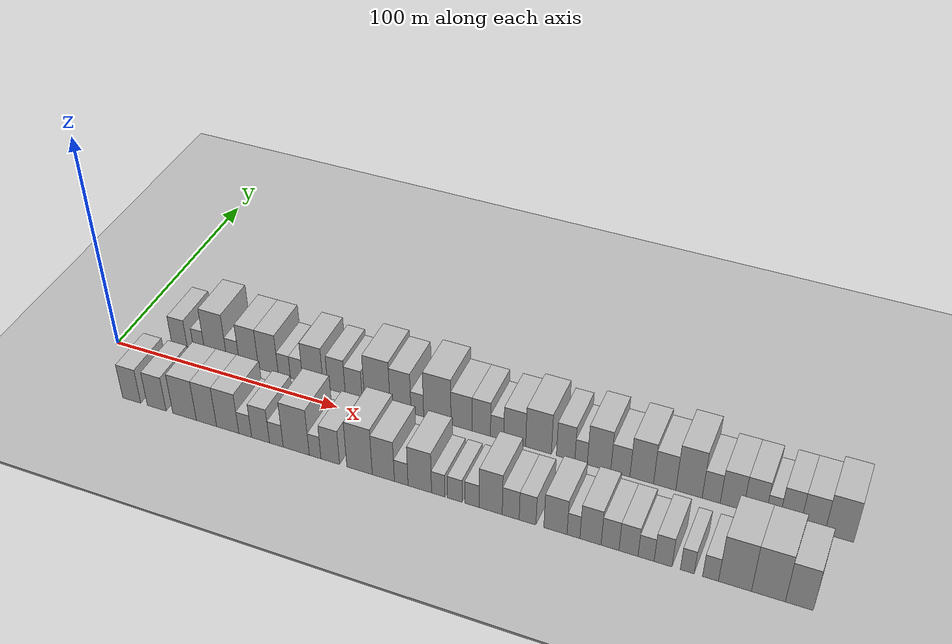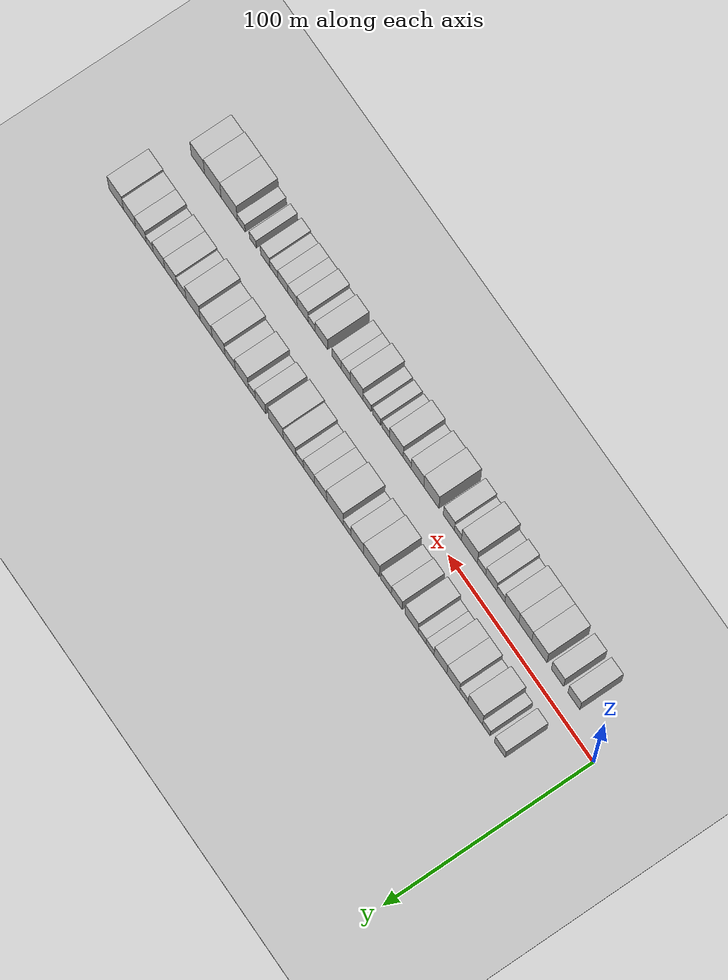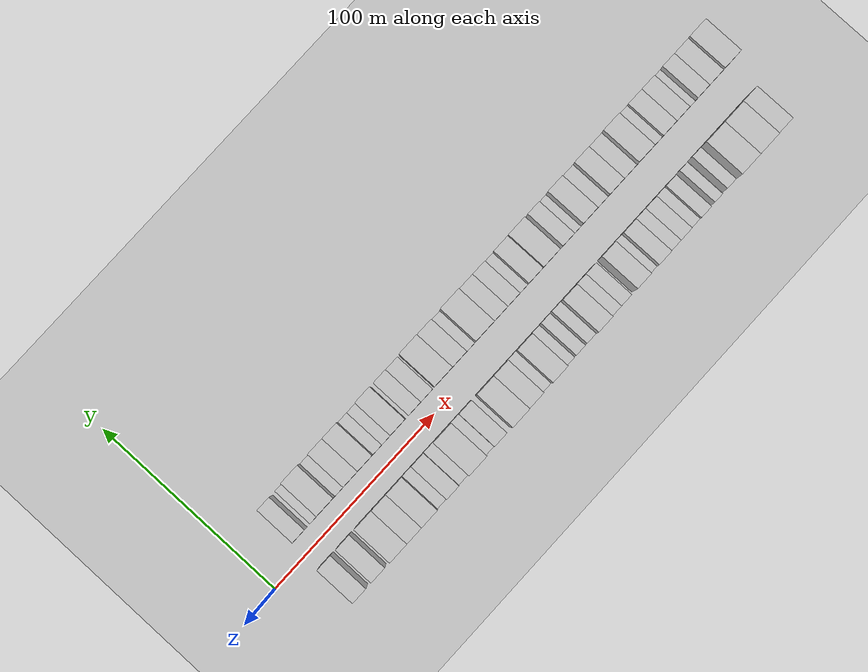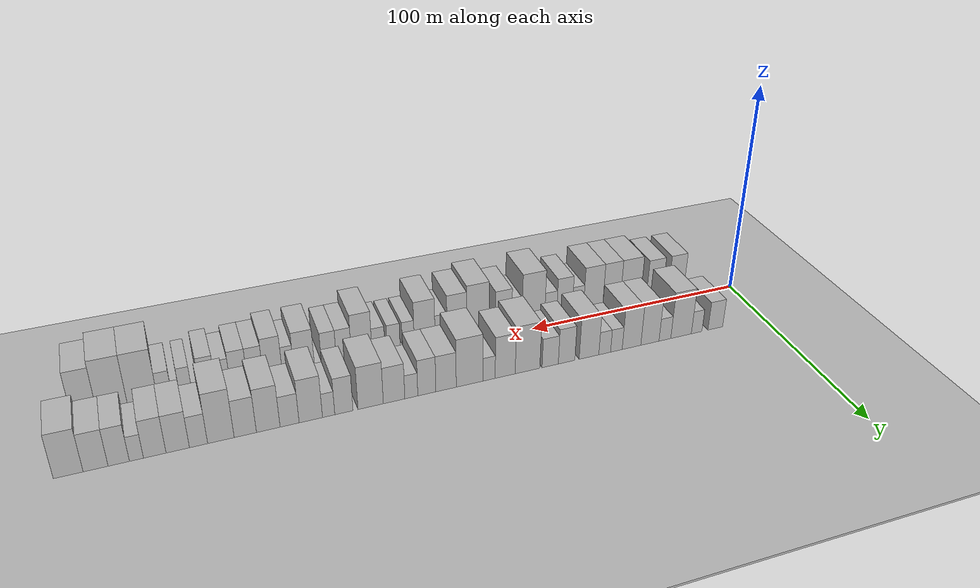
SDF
<?xml version="1.0" encoding="utf-8"?>

<sdf version="1.6">

   <world name="default">

      <gui fullscreen="0">

         <camera name="user_camera">

            <pose>-15 0 4.57585 0 0 0</pose>

            <view_controller>orbit</view_controller>

         </camera>

      </gui>

      <scene>

         <sky>

           <clouds>

             <speed>12</speed>

           </clouds>

         </sky>

         <ambient>0.4 0.4 0.4 1</ambient>

         <background>0.7 0.7 0.7 1</background>

         <shadows>1</shadows>

      </scene>

      <gravity>0 0 -9.8066</gravity>

      <magnetic_field>6e-06 2.3e-05 -4.2e-05</magnetic_field>

      <physics default="0" name="default_physics" type="ode">

         <ode>

            <solver>

               <type>quick</type>

               <iters>10</iters>

               <sor>1.0</sor>

               <use_dynamic_moi_rescaling>0</use_dynamic_moi_rescaling>

            </solver>

            <constraints>

               <cfm>0</cfm>

               <erp>0.2</erp>

               <contact_max_correcting_vel>100</contact_max_correcting_vel>

               <contact_surface_layer>0.001</contact_surface_layer>

            </constraints>

         </ode>

         <max_step_size>0.004</max_step_size>

         <real_time_factor>1</real_time_factor>

         <real_time_update_rate>250</real_time_update_rate>

      </physics>

      <light name="sun" type="directional">

         <cast_shadows>1</cast_shadows>

         <pose>0 0 10 0 0 0</pose>

         <diffuse>0.8 0.8 0.8 1</diffuse>

         <specular>0.2 0.2 0.2 1</specular>

         <attenuation>

            <range>1000</range>

            <constant>0.9</constant>

            <linear>0.01</linear>

            <quadratic>0.001</quadratic>

         </attenuation>

         <direction>-0.5 0.1 -0.9</direction>

      </light>

      <include>

         <name>ground_plane_1</name>

         <uri>model://HANNAS_ground_plane</uri>

         <pose>0 0 0  0 0 0</pose>

      </include>

      <include>

         <name>ground_plane_2</name>

         <uri>model://HANNAS_ground_plane</uri>

         <pose>100 0 0  0 0 0</pose>

      </include>

      <model name="building_1">

         <static>1</static>

         <pose frame="">24.6984 17.5000 0 0.000000 0.000000 1.570796</pose>

         <link name="link">

            <pose frame="">0 0 7.50 0 0 0</pose>

            <collision name="collision">

               <geometry>

                  <box>

                     <size>20.0000 7.3968 15.0000</size>

                  </box>

               </geometry>

               <max_contacts>10</max_contacts>

               <surface>

                  <contact>

                     <ode/>

                  </contact>

                  <bounce/>

                  <friction>

                     <torsional>

                        <ode/>

                     </torsional>

                     <ode/>

                  </friction>

               </surface>

            </collision>

            <visual name="visual">

               <cast_shadows>0</cast_shadows>

               <geometry>

                  <box>

                     <size>20.0000 7.3968 15.0000</size>

                  </box>

               </geometry>

               <material>

                  <script>

                     <uri>model://HANNAS_wall/materials/scripts</uri>

                     <uri>model://HANNAS_wall/materials/textures</uri>

                     <name>vrc/HANNAS_wall</name>

                  </script>

               </material>

            </visual>

            <self_collide>0</self_collide>

            <enable_wind>0</enable_wind>

            <kinematic>0</kinematic>

         </link>

      </model>

      <model name="building_2">

         <static>1</static>

         <pose frame="">34.0236 17.5000 0 0.000000 0.000000 1.570796</pose>

         <link name="link">

            <pose frame="">0 0 6.00 0 0 0</pose>

            <collision name="collision">

               <geometry>

                  <box>

                     <size>20.0000 5.2536 12.0000</size>

                  </box>

               </geometry>

               <max_contacts>10</max_contacts>

               <surface>

                  <contact>

                     <ode/>

                  </contact>

                  <bounce/>

                  <friction>

                     <torsional>

                        <ode/>

                     </torsional>

                     <ode/>

                  </friction>

               </surface>

            </collision>

            <visual name="visual">

               <cast_shadows>0</cast_shadows>

               <geometry>

                  <box>

                     <size>20.0000 5.2536 12.0000</size>

                  </box>

               </geometry>

               <material>

                  <script>

                     <uri>model://HANNAS_wall/materials/scripts</uri>

                     <uri>model://HANNAS_wall/materials/textures</uri>

                     <name>vrc/HANNAS_wall</name>

                  </script>

               </material>

            </visual>

            <self_collide>0</self_collide>

            <enable_wind>0</enable_wind>

            <kinematic>0</kinematic>

         </link>

      </model>

      <model name="building_3">

         <static>1</static>

         <pose frame="">41.7122 17.5000 0 0.000000 0.000000 1.570796</pose>

         <link name="link">

            <pose frame="">0 0 12.00 0 0 0</pose>

            <collision name="collision">

               <geometry>

                  <box>

                     <size>20.0000 10.1236 24.0000</size>

                  </box>

               </geometry>

               <max_contacts>10</max_contacts>

               <surface>

                  <contact>

                     <ode/>

                  </contact>

                  <bounce/>

                  <friction>

                     <torsional>

                        <ode/>

                     </torsional>

                     <ode/>

                  </friction>

               </surface>

            </collision>

            <visual name="visual">

               <cast_shadows>0</cast_shadows>

               <geometry>

                  <box>

                     <size>20.0000 10.1236 24.0000</size>

                  </box>

               </geometry>

               <material>

                  <script>

                     <uri>model://HANNAS_wall/materials/scripts</uri>

                     <uri>model://HANNAS_wall/materials/textures</uri>

                     <name>vrc/HANNAS_wall</name>

                  </script>

               </material>

            </visual>

            <self_collide>0</self_collide>

            <enable_wind>0</enable_wind>

            <kinematic>0</kinematic>

         </link>

      </model>

      <model name="building_4">

         <static>1</static>

         <pose frame="">49.6409 17.5000 0 0.000000 0.000000 1.570796</pose>

         <link name="link">

            <pose frame="">0 0 6.00 0 0 0</pose>

            <collision name="collision">

               <geometry>

                  <box>

                     <size>20.0000 5.7338 12.0000</size>

                  </box>

               </geometry>

               <max_contacts>10</max_contacts>

               <surface>

                  <contact>

                     <ode/>

                  </contact>

                  <bounce/>

                  <friction>

                     <torsional>

                        <ode/>

                     </torsional>

                     <ode/>

                  </friction>

               </surface>

            </collision>

            <visual name="visual">

               <cast_shadows>0</cast_shadows>

               <geometry>

                  <box>

                     <size>20.0000 5.7338 12.0000</size>

                  </box>

               </geometry>

               <material>

                  <script>

                     <uri>model://HANNAS_wall/materials/scripts</uri>

                     <uri>model://HANNAS_wall/materials/textures</uri>

                     <name>vrc/HANNAS_wall</name>

                  </script>

               </material>

            </visual>

            <self_collide>0</self_collide>

            <enable_wind>0</enable_wind>

            <kinematic>0</kinematic>

         </link>

      </model>

      <model name="building_5">

         <static>1</static>

         <pose frame="">56.8956 17.5000 0 0.000000 0.000000 1.570796</pose>

         <link name="link">

            <pose frame="">0 0 10.50 0 0 0</pose>

            <collision name="collision">

               <geometry>

                  <box>

                     <size>20.0000 8.7756 21.0000</size>

                  </box>

               </geometry>

               <max_contacts>10</max_contacts>

               <surface>

                  <contact>

                     <ode/>

                  </contact>

                  <bounce/>

                  <friction>

                     <torsional>

                        <ode/>

                     </torsional>

                     <ode/>

                  </friction>

               </surface>

            </collision>

            <visual name="visual">

               <cast_shadows>0</cast_shadows>

               <geometry>

                  <box>

                     <size>20.0000 8.7756 21.0000</size>

                  </box>

               </geometry>

               <material>

                  <script>

                     <uri>model://HANNAS_wall/materials/scripts</uri>

                     <uri>model://HANNAS_wall/materials/textures</uri>

                     <name>vrc/HANNAS_wall</name>

                  </script>

               </material>

            </visual>

            <self_collide>0</self_collide>

            <enable_wind>0</enable_wind>

            <kinematic>0</kinematic>

         </link>

      </model>

      <model name="building_6">

         <static>1</static>

         <pose frame="">65.7322 17.5000 0 0.000000 0.000000 1.570796</pose>

         <link name="link">

            <pose frame="">0 0 10.50 0 0 0</pose>

            <collision name="collision">

               <geometry>

                  <box>

                     <size>20.0000 8.8976 21.0000</size>

                  </box>

               </geometry>

               <max_contacts>10</max_contacts>

               <surface>

                  <contact>

                     <ode/>

                  </contact>

                  <bounce/>

                  <friction>

                     <torsional>

                        <ode/>

                     </torsional>

                     <ode/>

                  </friction>

               </surface>

            </collision>

            <visual name="visual">

               <cast_shadows>0</cast_shadows>

               <geometry>

                  <box>

                     <size>20.0000 8.8976 21.0000</size>

                  </box>

               </geometry>

               <material>

                  <script>

                     <uri>model://HANNAS_wall/materials/scripts</uri>

                     <uri>model://HANNAS_wall/materials/textures</uri>

                     <name>vrc/HANNAS_wall</name>

                  </script>

               </material>

            </visual>

            <self_collide>0</self_collide>

            <enable_wind>0</enable_wind>

            <kinematic>0</kinematic>

         </link>

      </model>

      <model name="building_7">

         <static>1</static>

         <pose frame="">72.9210 17.5000 0 0.000000 0.000000 1.570796</pose>

         <link name="link">

            <pose frame="">0 0 6.00 0 0 0</pose>

            <collision name="collision">

               <geometry>

                  <box>

                     <size>20.0000 5.4799 12.0000</size>

                  </box>

               </geometry>

               <max_contacts>10</max_contacts>

               <surface>

                  <contact>

                     <ode/>

                  </contact>

                  <bounce/>

                  <friction>

                     <torsional>

                        <ode/>

                     </torsional>

                     <ode/>

                  </friction>

               </surface>

            </collision>

            <visual name="visual">

               <cast_shadows>0</cast_shadows>

               <geometry>

                  <box>

                     <size>20.0000 5.4799 12.0000</size>

                  </box>

               </geometry>

               <material>

                  <script>

                     <uri>model://HANNAS_wall/materials/scripts</uri>

                     <uri>model://HANNAS_wall/materials/textures</uri>

                     <name>vrc/HANNAS_wall</name>

                  </script>

               </material>

            </visual>

            <self_collide>0</self_collide>

            <enable_wind>0</enable_wind>

            <kinematic>0</kinematic>

         </link>

      </model>

      <model name="building_8">

         <static>1</static>

         <pose frame="">78.4243 17.5000 0 0.000000 0.000000 1.570796</pose>

         <link name="link">

            <pose frame="">0 0 6.00 0 0 0</pose>

            <collision name="collision">

               <geometry>

                  <box>

                     <size>20.0000 5.5267 12.0000</size>

                  </box>

               </geometry>

               <max_contacts>10</max_contacts>

               <surface>

                  <contact>

                     <ode/>

                  </contact>

                  <bounce/>

                  <friction>

                     <torsional>

                        <ode/>

                     </torsional>

                     <ode/>

                  </friction>

               </surface>

            </collision>

            <visual name="visual">

               <cast_shadows>0</cast_shadows>

               <geometry>

                  <box>

                     <size>20.0000 5.5267 12.0000</size>

                  </box>

               </geometry>

               <material>

                  <script>

                     <uri>model://HANNAS_wall/materials/scripts</uri>

                     <uri>model://HANNAS_wall/materials/textures</uri>

                     <name>vrc/HANNAS_wall</name>

                  </script>

               </material>

            </visual>

            <self_collide>0</self_collide>

            <enable_wind>0</enable_wind>

            <kinematic>0</kinematic>

         </link>

      </model>

      <model name="building_9">

         <static>1</static>

         <pose frame="">85.7504 17.5000 0 0.000000 0.000000 1.570796</pose>

         <link name="link">

            <pose frame="">0 0 10.50 0 0 0</pose>

            <collision name="collision">

               <geometry>

                  <box>

                     <size>20.0000 9.1255 21.0000</size>

                  </box>

               </geometry>

               <max_contacts>10</max_contacts>

               <surface>

                  <contact>

                     <ode/>

                  </contact>

                  <bounce/>

                  <friction>

                     <torsional>

                        <ode/>

                     </torsional>

                     <ode/>

                  </friction>

               </surface>

            </collision>

            <visual name="visual">

               <cast_shadows>0</cast_shadows>

               <geometry>

                  <box>

                     <size>20.0000 9.1255 21.0000</size>

                  </box>

               </geometry>

               <material>

                  <script>

                     <uri>model://HANNAS_wall/materials/scripts</uri>

                     <uri>model://HANNAS_wall/materials/textures</uri>

                     <name>vrc/HANNAS_wall</name>

                  </script>

               </material>

            </visual>

            <self_collide>0</self_collide>

            <enable_wind>0</enable_wind>

            <kinematic>0</kinematic>

         </link>

      </model>

      <model name="building_10">

         <static>1</static>

         <pose frame="">96.1043 17.5000 0 0.000000 0.000000 1.570796</pose>

         <link name="link">

            <pose frame="">0 0 9.00 0 0 0</pose>

            <collision name="collision">

               <geometry>

                  <box>

                     <size>20.0000 7.5824 18.0000</size>

                  </box>

               </geometry>

               <max_contacts>10</max_contacts>

               <surface>

                  <contact>

                     <ode/>

                  </contact>

                  <bounce/>

                  <friction>

                     <torsional>

                        <ode/>

                     </torsional>

                     <ode/>

                  </friction>

               </surface>

            </collision>

            <visual name="visual">

               <cast_shadows>0</cast_shadows>

               <geometry>

                  <box>

                     <size>20.0000 7.5824 18.0000</size>

                  </box>

               </geometry>

               <material>

                  <script>

                     <uri>model://HANNAS_wall/materials/scripts</uri>

                     <uri>model://HANNAS_wall/materials/textures</uri>

                     <name>vrc/HANNAS_wall</name>

                  </script>

               </material>

            </visual>

            <self_collide>0</self_collide>

            <enable_wind>0</enable_wind>

            <kinematic>0</kinematic>

         </link>

      </model>

      <model name="building_11">

         <static>1</static>

         <pose frame="">103.5795 17.5000 0 0.000000 0.000000 1.570796</pose>

         <link name="link">

            <pose frame="">0 0 7.50 0 0 0</pose>

            <collision name="collision">

               <geometry>

                  <box>

                     <size>20.0000 7.3680 15.0000</size>

                  </box>

               </geometry>

               <max_contacts>10</max_contacts>

               <surface>

                  <contact>

                     <ode/>

                  </contact>

                  <bounce/>

                  <friction>

                     <torsional>

                        <ode/>

                     </torsional>

                     <ode/>

                  </friction>

               </surface>

            </collision>

            <visual name="visual">

               <cast_shadows>0</cast_shadows>

               <geometry>

                  <box>

                     <size>20.0000 7.3680 15.0000</size>

                  </box>

               </geometry>

               <material>

                  <script>

                     <uri>model://HANNAS_wall/materials/scripts</uri>

                     <uri>model://HANNAS_wall/materials/textures</uri>

                     <name>vrc/HANNAS_wall</name>

                  </script>

               </material>

            </visual>

            <self_collide>0</self_collide>

            <enable_wind>0</enable_wind>

            <kinematic>0</kinematic>

         </link>

      </model>

      <model name="building_12">

         <static>1</static>

         <pose frame="">113.7813 17.5000 0 0.000000 0.000000 1.570796</pose>

         <link name="link">

            <pose frame="">0 0 12.00 0 0 0</pose>

            <collision name="collision">

               <geometry>

                  <box>

                     <size>20.0000 11.0357 24.0000</size>

                  </box>

               </geometry>

               <max_contacts>10</max_contacts>

               <surface>

                  <contact>

                     <ode/>

                  </contact>

                  <bounce/>

                  <friction>

                     <torsional>

                        <ode/>

                     </torsional>

                     <ode/>

                  </friction>

               </surface>

            </collision>

            <visual name="visual">

               <cast_shadows>0</cast_shadows>

               <geometry>

                  <box>

                     <size>20.0000 11.0357 24.0000</size>

                  </box>

               </geometry>

               <material>

                  <script>

                     <uri>model://HANNAS_wall/materials/scripts</uri>

                     <uri>model://HANNAS_wall/materials/textures</uri>

                     <name>vrc/HANNAS_wall</name>

                  </script>

               </material>

            </visual>

            <self_collide>0</self_collide>

            <enable_wind>0</enable_wind>

            <kinematic>0</kinematic>

         </link>

      </model>

      <model name="building_13">

         <static>1</static>

         <pose frame="">123.7441 17.5000 0 0.000000 0.000000 1.570796</pose>

         <link name="link">

            <pose frame="">0 0 10.50 0 0 0</pose>

            <collision name="collision">

               <geometry>

                  <box>

                     <size>20.0000 8.8899 21.0000</size>

                  </box>

               </geometry>

               <max_contacts>10</max_contacts>

               <surface>

                  <contact>

                     <ode/>

                  </contact>

                  <bounce/>

                  <friction>

                     <torsional>

                        <ode/>

                     </torsional>

                     <ode/>

                  </friction>

               </surface>

            </collision>

            <visual name="visual">

               <cast_shadows>0</cast_shadows>

               <geometry>

                  <box>

                     <size>20.0000 8.8899 21.0000</size>

                  </box>

               </geometry>

               <material>

                  <script>

                     <uri>model://HANNAS_wall/materials/scripts</uri>

                     <uri>model://HANNAS_wall/materials/textures</uri>

                     <name>vrc/HANNAS_wall</name>

                  </script>

               </material>

            </visual>

            <self_collide>0</self_collide>

            <enable_wind>0</enable_wind>

            <kinematic>0</kinematic>

         </link>

      </model>

      <model name="building_14">

         <static>1</static>

         <pose frame="">130.8703 17.5000 0 0.000000 0.000000 1.570796</pose>

         <link name="link">

            <pose frame="">0 0 6.00 0 0 0</pose>

            <collision name="collision">

               <geometry>

                  <box>

                     <size>20.0000 5.3623 12.0000</size>

                  </box>

               </geometry>

               <max_contacts>10</max_contacts>

               <surface>

                  <contact>

                     <ode/>

                  </contact>

                  <bounce/>

                  <friction>

                     <torsional>

                        <ode/>

                     </torsional>

                     <ode/>

                  </friction>

               </surface>

            </collision>

            <visual name="visual">

               <cast_shadows>0</cast_shadows>

               <geometry>

                  <box>

                     <size>20.0000 5.3623 12.0000</size>

                  </box>

               </geometry>

               <material>

                  <script>

                     <uri>model://HANNAS_wall/materials/scripts</uri>

                     <uri>model://HANNAS_wall/materials/textures</uri>

                     <name>vrc/HANNAS_wall</name>

                  </script>

               </material>

            </visual>

            <self_collide>0</self_collide>

            <enable_wind>0</enable_wind>

            <kinematic>0</kinematic>

         </link>

      </model>

      <model name="building_15">

         <static>1</static>

         <pose frame="">139.3018 17.5000 0 0.000000 0.000000 1.570796</pose>

         <link name="link">

            <pose frame="">0 0 12.00 0 0 0</pose>

            <collision name="collision">

               <geometry>

                  <box>

                     <size>20.0000 11.5008 24.0000</size>

                  </box>

               </geometry>

               <max_contacts>10</max_contacts>

               <surface>

                  <contact>

                     <ode/>

                  </contact>

                  <bounce/>

                  <friction>

                     <torsional>

                        <ode/>

                     </torsional>

                     <ode/>

                  </friction>

               </surface>

            </collision>

            <visual name="visual">

               <cast_shadows>0</cast_shadows>

               <geometry>

                  <box>

                     <size>20.0000 11.5008 24.0000</size>

                  </box>

               </geometry>

               <material>

                  <script>

                     <uri>model://HANNAS_wall/materials/scripts</uri>

                     <uri>model://HANNAS_wall/materials/textures</uri>

                     <name>vrc/HANNAS_wall</name>

                  </script>

               </material>

            </visual>

            <self_collide>0</self_collide>

            <enable_wind>0</enable_wind>

            <kinematic>0</kinematic>

         </link>

      </model>

      <model name="building_16">

         <static>1</static>

         <pose frame="">149.3966 17.5000 0 0.000000 0.000000 1.570796</pose>

         <link name="link">

            <pose frame="">0 0 9.00 0 0 0</pose>

            <collision name="collision">

               <geometry>

                  <box>

                     <size>20.0000 8.6888 18.0000</size>

                  </box>

               </geometry>

               <max_contacts>10</max_contacts>

               <surface>

                  <contact>

                     <ode/>

                  </contact>

                  <bounce/>

                  <friction>

                     <torsional>

                        <ode/>

                     </torsional>

                     <ode/>

                  </friction>

               </surface>

            </collision>

            <visual name="visual">

               <cast_shadows>0</cast_shadows>

               <geometry>

                  <box>

                     <size>20.0000 8.6888 18.0000</size>

                  </box>

               </geometry>

               <material>

                  <script>

                     <uri>model://HANNAS_wall/materials/scripts</uri>

                     <uri>model://HANNAS_wall/materials/textures</uri>

                     <name>vrc/HANNAS_wall</name>

                  </script>

               </material>

            </visual>

            <self_collide>0</self_collide>

            <enable_wind>0</enable_wind>

            <kinematic>0</kinematic>

         </link>

      </model>

      <model name="building_17">

         <static>1</static>

         <pose frame="">157.5444 17.5000 0 0.000000 0.000000 1.570796</pose>

         <link name="link">

            <pose frame="">0 0 9.00 0 0 0</pose>

            <collision name="collision">

               <geometry>

                  <box>

                     <size>20.0000 7.6067 18.0000</size>

                  </box>

               </geometry>

               <max_contacts>10</max_contacts>

               <surface>

                  <contact>

                     <ode/>

                  </contact>

                  <bounce/>

                  <friction>

                     <torsional>

                        <ode/>

                     </torsional>

                     <ode/>

                  </friction>

               </surface>

            </collision>

            <visual name="visual">

               <cast_shadows>0</cast_shadows>

               <geometry>

                  <box>

                     <size>20.0000 7.6067 18.0000</size>

                  </box>

               </geometry>

               <material>

                  <script>

                     <uri>model://HANNAS_wall/materials/scripts</uri>

                     <uri>model://HANNAS_wall/materials/textures</uri>

                     <name>vrc/HANNAS_wall</name>

                  </script>

               </material>

            </visual>

            <self_collide>0</self_collide>

            <enable_wind>0</enable_wind>

            <kinematic>0</kinematic>

         </link>

      </model>

      <model name="building_18">

         <static>1</static>

         <pose frame="">164.0554 17.5000 0 0.000000 0.000000 1.570796</pose>

         <link name="link">

            <pose frame="">0 0 6.00 0 0 0</pose>

            <collision name="collision">

               <geometry>

                  <box>

                     <size>20.0000 5.4154 12.0000</size>

                  </box>

               </geometry>

               <max_contacts>10</max_contacts>

               <surface>

                  <contact>

                     <ode/>

                  </contact>

                  <bounce/>

                  <friction>

                     <torsional>

                        <ode/>

                     </torsional>

                     <ode/>

                  </friction>

               </surface>

            </collision>

            <visual name="visual">

               <cast_shadows>0</cast_shadows>

               <geometry>

                  <box>

                     <size>20.0000 5.4154 12.0000</size>

                  </box>

               </geometry>

               <material>

                  <script>

                     <uri>model://HANNAS_wall/materials/scripts</uri>

                     <uri>model://HANNAS_wall/materials/textures</uri>

                     <name>vrc/HANNAS_wall</name>

                  </script>

               </material>

            </visual>

            <self_collide>0</self_collide>

            <enable_wind>0</enable_wind>

            <kinematic>0</kinematic>

         </link>

      </model>

      <model name="building_19">

         <static>1</static>

         <pose frame="">171.2047 17.5000 0 0.000000 0.000000 1.570796</pose>

         <link name="link">

            <pose frame="">0 0 9.00 0 0 0</pose>

            <collision name="collision">

               <geometry>

                  <box>

                     <size>20.0000 8.8832 18.0000</size>

                  </box>

               </geometry>

               <max_contacts>10</max_contacts>

               <surface>

                  <contact>

                     <ode/>

                  </contact>

                  <bounce/>

                  <friction>

                     <torsional>

                        <ode/>

                     </torsional>

                     <ode/>

                  </friction>

               </surface>

            </collision>

            <visual name="visual">

               <cast_shadows>0</cast_shadows>

               <geometry>

                  <box>

                     <size>20.0000 8.8832 18.0000</size>

                  </box>

               </geometry>

               <material>

                  <script>

                     <uri>model://HANNAS_wall/materials/scripts</uri>

                     <uri>model://HANNAS_wall/materials/textures</uri>

                     <name>vrc/HANNAS_wall</name>

                  </script>

               </material>

            </visual>

            <self_collide>0</self_collide>

            <enable_wind>0</enable_wind>

            <kinematic>0</kinematic>

         </link>

      </model>

      <model name="building_20">

         <static>1</static>

         <pose frame="">180.8166 17.5000 0 0.000000 0.000000 1.570796</pose>

         <link name="link">

            <pose frame="">0 0 10.50 0 0 0</pose>

            <collision name="collision">

               <geometry>

                  <box>

                     <size>20.0000 10.3407 21.0000</size>

                  </box>

               </geometry>

               <max_contacts>10</max_contacts>

               <surface>

                  <contact>

                     <ode/>

                  </contact>

                  <bounce/>

                  <friction>

                     <torsional>

                        <ode/>

                     </torsional>

                     <ode/>

                  </friction>

               </surface>

            </collision>

            <visual name="visual">

               <cast_shadows>0</cast_shadows>

               <geometry>

                  <box>

                     <size>20.0000 10.3407 21.0000</size>

                  </box>

               </geometry>

               <material>

                  <script>

                     <uri>model://HANNAS_wall/materials/scripts</uri>

                     <uri>model://HANNAS_wall/materials/textures</uri>

                     <name>vrc/HANNAS_wall</name>

                  </script>

               </material>

            </visual>

            <self_collide>0</self_collide>

            <enable_wind>0</enable_wind>

            <kinematic>0</kinematic>

         </link>

      </model>

      <model name="building_21">

         <static>1</static>

         <pose frame="">191.6453 17.5000 0 0.000000 0.000000 1.570796</pose>

         <link name="link">

            <pose frame="">0 0 9.00 0 0 0</pose>

            <collision name="collision">

               <geometry>

                  <box>

                     <size>20.0000 7.3166 18.0000</size>

                  </box>

               </geometry>

               <max_contacts>10</max_contacts>

               <surface>

                  <contact>

                     <ode/>

                  </contact>

                  <bounce/>

                  <friction>

                     <torsional>

                        <ode/>

                     </torsional>

                     <ode/>

                  </friction>

               </surface>

            </collision>

            <visual name="visual">

               <cast_shadows>0</cast_shadows>

               <geometry>

                  <box>

                     <size>20.0000 7.3166 18.0000</size>

                  </box>

               </geometry>

               <material>

                  <script>

                     <uri>model://HANNAS_wall/materials/scripts</uri>

                     <uri>model://HANNAS_wall/materials/textures</uri>

                     <name>vrc/HANNAS_wall</name>

                  </script>

               </material>

            </visual>

            <self_collide>0</self_collide>

            <enable_wind>0</enable_wind>

            <kinematic>0</kinematic>

         </link>

      </model>

      <model name="building_22">

         <static>1</static>

         <pose frame="">197.7555 17.5000 0 0.000000 0.000000 1.570796</pose>

         <link name="link">

            <pose frame="">0 0 6.00 0 0 0</pose>

            <collision name="collision">

               <geometry>

                  <box>

                     <size>20.0000 4.9037 12.0000</size>

                  </box>

               </geometry>

               <max_contacts>10</max_contacts>

               <surface>

                  <contact>

                     <ode/>

                  </contact>

                  <bounce/>

                  <friction>

                     <torsional>

                        <ode/>

                     </torsional>

                     <ode/>

                  </friction>

               </surface>

            </collision>

            <visual name="visual">

               <cast_shadows>0</cast_shadows>

               <geometry>

                  <box>

                     <size>20.0000 4.9037 12.0000</size>

                  </box>

               </geometry>

               <material>

                  <script>

                     <uri>model://HANNAS_wall/materials/scripts</uri>

                     <uri>model://HANNAS_wall/materials/textures</uri>

                     <name>vrc/HANNAS_wall</name>

                  </script>

               </material>

            </visual>

            <self_collide>0</self_collide>

            <enable_wind>0</enable_wind>

            <kinematic>0</kinematic>

         </link>

      </model>

      <model name="building_23">

         <static>1</static>

         <pose frame="">204.8194 17.5000 0 0.000000 0.000000 1.570796</pose>

         <link name="link">

            <pose frame="">0 0 10.50 0 0 0</pose>

            <collision name="collision">

               <geometry>

                  <box>

                     <size>20.0000 9.2242 21.0000</size>

                  </box>

               </geometry>

               <max_contacts>10</max_contacts>

               <surface>

                  <contact>

                     <ode/>

                  </contact>

                  <bounce/>

                  <friction>

                     <torsional>

                        <ode/>

                     </torsional>

                     <ode/>

                  </friction>

               </surface>

            </collision>

            <visual name="visual">

               <cast_shadows>0</cast_shadows>

               <geometry>

                  <box>

                     <size>20.0000 9.2242 21.0000</size>

                  </box>

               </geometry>

               <material>

                  <script>

                     <uri>model://HANNAS_wall/materials/scripts</uri>

                     <uri>model://HANNAS_wall/materials/textures</uri>

                     <name>vrc/HANNAS_wall</name>

                  </script>

               </material>

            </visual>

            <self_collide>0</self_collide>

            <enable_wind>0</enable_wind>

            <kinematic>0</kinematic>

         </link>

      </model>

      <model name="building_24">

         <static>1</static>

         <pose frame="">213.1341 17.5000 0 0.000000 0.000000 1.570796</pose>

         <link name="link">

            <pose frame="">0 0 7.50 0 0 0</pose>

            <collision name="collision">

               <geometry>

                  <box>

                     <size>20.0000 7.4053 15.0000</size>

                  </box>

               </geometry>

               <max_contacts>10</max_contacts>

               <surface>

                  <contact>

                     <ode/>

                  </contact>

                  <bounce/>

                  <friction>

                     <torsional>

                        <ode/>

                     </torsional>

                     <ode/>

                  </friction>

               </surface>

            </collision>

            <visual name="visual">

               <cast_shadows>0</cast_shadows>

               <geometry>

                  <box>

                     <size>20.0000 7.4053 15.0000</size>

                  </box>

               </geometry>

               <material>

                  <script>

                     <uri>model://HANNAS_wall/materials/scripts</uri>

                     <uri>model://HANNAS_wall/materials/textures</uri>

                     <name>vrc/HANNAS_wall</name>

                  </script>

               </material>

            </visual>

            <self_collide>0</self_collide>

            <enable_wind>0</enable_wind>

            <kinematic>0</kinematic>

         </link>

      </model>

      <model name="building_25">

         <static>1</static>

         <pose frame="">221.3906 17.5000 0 0.000000 0.000000 1.570796</pose>

         <link name="link">

            <pose frame="">0 0 10.50 0 0 0</pose>

            <collision name="collision">

               <geometry>

                  <box>

                     <size>20.0000 9.1077 21.0000</size>

                  </box>

               </geometry>

               <max_contacts>10</max_contacts>

               <surface>

                  <contact>

                     <ode/>

                  </contact>

                  <bounce/>

                  <friction>

                     <torsional>

                        <ode/>

                     </torsional>

                     <ode/>

                  </friction>

               </surface>

            </collision>

            <visual name="visual">

               <cast_shadows>0</cast_shadows>

               <geometry>

                  <box>

                     <size>20.0000 9.1077 21.0000</size>

                  </box>

               </geometry>

               <material>

                  <script>

                     <uri>model://HANNAS_wall/materials/scripts</uri>

                     <uri>model://HANNAS_wall/materials/textures</uri>

                     <name>vrc/HANNAS_wall</name>

                  </script>

               </material>

            </visual>

            <self_collide>0</self_collide>

            <enable_wind>0</enable_wind>

            <kinematic>0</kinematic>

         </link>

      </model>

      <model name="building_26">

         <static>1</static>

         <pose frame="">230.1751 17.5000 0 0.000000 0.000000 1.570796</pose>

         <link name="link">

            <pose frame="">0 0 9.00 0 0 0</pose>

            <collision name="collision">

               <geometry>

                  <box>

                     <size>20.0000 8.4612 18.0000</size>

                  </box>

               </geometry>

               <max_contacts>10</max_contacts>

               <surface>

                  <contact>

                     <ode/>

                  </contact>

                  <bounce/>

                  <friction>

                     <torsional>

                        <ode/>

                     </torsional>

                     <ode/>

                  </friction>

               </surface>

            </collision>

            <visual name="visual">

               <cast_shadows>0</cast_shadows>

               <geometry>

                  <box>

                     <size>20.0000 8.4612 18.0000</size>

                  </box>

               </geometry>

               <material>

                  <script>

                     <uri>model://HANNAS_wall/materials/scripts</uri>

                     <uri>model://HANNAS_wall/materials/textures</uri>

                     <name>vrc/HANNAS_wall</name>

                  </script>

               </material>

            </visual>

            <self_collide>0</self_collide>

            <enable_wind>0</enable_wind>

            <kinematic>0</kinematic>

         </link>

      </model>

      <model name="building_27">

         <static>1</static>

         <pose frame="">239.3785 17.5000 0 0.000000 0.000000 1.570796</pose>

         <link name="link">

            <pose frame="">0 0 12.00 0 0 0</pose>

            <collision name="collision">

               <geometry>

                  <box>

                     <size>20.0000 9.9455 24.0000</size>

                  </box>

               </geometry>

               <max_contacts>10</max_contacts>

               <surface>

                  <contact>

                     <ode/>

                  </contact>

                  <bounce/>

                  <friction>

                     <torsional>

                        <ode/>

                     </torsional>

                     <ode/>

                  </friction>

               </surface>

            </collision>

            <visual name="visual">

               <cast_shadows>0</cast_shadows>

               <geometry>

                  <box>

                     <size>20.0000 9.9455 24.0000</size>

                  </box>

               </geometry>

               <material>

                  <script>

                     <uri>model://HANNAS_wall/materials/scripts</uri>

                     <uri>model://HANNAS_wall/materials/textures</uri>

                     <name>vrc/HANNAS_wall</name>

                  </script>

               </material>

            </visual>

            <self_collide>0</self_collide>

            <enable_wind>0</enable_wind>

            <kinematic>0</kinematic>

         </link>

      </model>

      <model name="building_28">

         <static>1</static>

         <pose frame="">247.7230 17.5000 0 0.000000 0.000000 1.570796</pose>

         <link name="link">

            <pose frame="">0 0 7.50 0 0 0</pose>

            <collision name="collision">

               <geometry>

                  <box>

                     <size>20.0000 6.7434 15.0000</size>

                  </box>

               </geometry>

               <max_contacts>10</max_contacts>

               <surface>

                  <contact>

                     <ode/>

                  </contact>

                  <bounce/>

                  <friction>

                     <torsional>

                        <ode/>

                     </torsional>

                     <ode/>

                  </friction>

               </surface>

            </collision>

            <visual name="visual">

               <cast_shadows>0</cast_shadows>

               <geometry>

                  <box>

                     <size>20.0000 6.7434 15.0000</size>

                  </box>

               </geometry>

               <material>

                  <script>

                     <uri>model://HANNAS_wall/materials/scripts</uri>

                     <uri>model://HANNAS_wall/materials/textures</uri>

                     <name>vrc/HANNAS_wall</name>

                  </script>

               </material>

            </visual>

            <self_collide>0</self_collide>

            <enable_wind>0</enable_wind>

            <kinematic>0</kinematic>

         </link>

      </model>

      <model name="building_29">

         <static>1</static>

         <pose frame="">255.3765 17.5000 0 0.000000 0.000000 1.570796</pose>

         <link name="link">

            <pose frame="">0 0 9.00 0 0 0</pose>

            <collision name="collision">

               <geometry>

                  <box>

                     <size>20.0000 8.5637 18.0000</size>

                  </box>

               </geometry>

               <max_contacts>10</max_contacts>

               <surface>

                  <contact>

                     <ode/>

                  </contact>

                  <bounce/>

                  <friction>

                     <torsional>

                        <ode/>

                     </torsional>

                     <ode/>

                  </friction>

               </surface>

            </collision>

            <visual name="visual">

               <cast_shadows>0</cast_shadows>

               <geometry>

                  <box>

                     <size>20.0000 8.5637 18.0000</size>

                  </box>

               </geometry>

               <material>

                  <script>

                     <uri>model://HANNAS_wall/materials/scripts</uri>

                     <uri>model://HANNAS_wall/materials/textures</uri>

                     <name>vrc/HANNAS_wall</name>

                  </script>

               </material>

            </visual>

            <self_collide>0</self_collide>

            <enable_wind>0</enable_wind>

            <kinematic>0</kinematic>

         </link>

      </model>

      <model name="building_30">

         <static>1</static>

         <pose frame="">263.7326 17.5000 0 0.000000 0.000000 1.570796</pose>

         <link name="link">

            <pose frame="">0 0 9.00 0 0 0</pose>

            <collision name="collision">

               <geometry>

                  <box>

                     <size>20.0000 8.1484 18.0000</size>

                  </box>

               </geometry>

               <max_contacts>10</max_contacts>

               <surface>

                  <contact>

                     <ode/>

                  </contact>

                  <bounce/>

                  <friction>

                     <torsional>

                        <ode/>

                     </torsional>

                     <ode/>

                  </friction>

               </surface>

            </collision>

            <visual name="visual">

               <cast_shadows>0</cast_shadows>

               <geometry>

                  <box>

                     <size>20.0000 8.1484 18.0000</size>

                  </box>

               </geometry>

               <material>

                  <script>

                     <uri>model://HANNAS_wall/materials/scripts</uri>

                     <uri>model://HANNAS_wall/materials/textures</uri>

                     <name>vrc/HANNAS_wall</name>

                  </script>

               </material>

            </visual>

            <self_collide>0</self_collide>

            <enable_wind>0</enable_wind>

            <kinematic>0</kinematic>

         </link>

      </model>

      <model name="building_31">

         <static>1</static>

         <pose frame="">270.3282 17.5000 0 0.000000 0.000000 1.570796</pose>

         <link name="link">

            <pose frame="">0 0 6.00 0 0 0</pose>

            <collision name="collision">

               <geometry>

                  <box>

                     <size>20.0000 5.0429 12.0000</size>

                  </box>

               </geometry>

               <max_contacts>10</max_contacts>

               <surface>

                  <contact>

                     <ode/>

                  </contact>

                  <bounce/>

                  <friction>

                     <torsional>

                        <ode/>

                     </torsional>

                     <ode/>

                  </friction>

               </surface>

            </collision>

            <visual name="visual">

               <cast_shadows>0</cast_shadows>

               <geometry>

                  <box>

                     <size>20.0000 5.0429 12.0000</size>

                  </box>

               </geometry>

               <material>

                  <script>

                     <uri>model://HANNAS_wall/materials/scripts</uri>

                     <uri>model://HANNAS_wall/materials/textures</uri>

                     <name>vrc/HANNAS_wall</name>

                  </script>

               </material>

            </visual>

            <self_collide>0</self_collide>

            <enable_wind>0</enable_wind>

            <kinematic>0</kinematic>

         </link>

      </model>

      <model name="building_32">

         <static>1</static>

         <pose frame="">276.6278 17.5000 0 0.000000 0.000000 1.570796</pose>

         <link name="link">

            <pose frame="">0 0 9.00 0 0 0</pose>

            <collision name="collision">

               <geometry>

                  <box>

                     <size>20.0000 7.5561 18.0000</size>

                  </box>

               </geometry>

               <max_contacts>10</max_contacts>

               <surface>

                  <contact>

                     <ode/>

                  </contact>

                  <bounce/>

                  <friction>

                     <torsional>

                        <ode/>

                     </torsional>

                     <ode/>

                  </friction>

               </surface>

            </collision>

            <visual name="visual">

               <cast_shadows>0</cast_shadows>

               <geometry>

                  <box>

                     <size>20.0000 7.5561 18.0000</size>

                  </box>

               </geometry>

               <material>

                  <script>

                     <uri>model://HANNAS_wall/materials/scripts</uri>

                     <uri>model://HANNAS_wall/materials/textures</uri>

                     <name>vrc/HANNAS_wall</name>

                  </script>

               </material>

            </visual>

            <self_collide>0</self_collide>

            <enable_wind>0</enable_wind>

            <kinematic>0</kinematic>

         </link>

      </model>

      <model name="building_33">

         <static>1</static>

         <pose frame="">284.7762 17.5000 0 0.000000 0.000000 1.570796</pose>

         <link name="link">

            <pose frame="">0 0 9.00 0 0 0</pose>

            <collision name="collision">

               <geometry>

                  <box>

                     <size>20.0000 8.7407 18.0000</size>

                  </box>

               </geometry>

               <max_contacts>10</max_contacts>

               <surface>

                  <contact>

                     <ode/>

                  </contact>

                  <bounce/>

                  <friction>

                     <torsional>

                        <ode/>

                     </torsional>

                     <ode/>

                  </friction>

               </surface>

            </collision>

            <visual name="visual">

               <cast_shadows>0</cast_shadows>

               <geometry>

                  <box>

                     <size>20.0000 8.7407 18.0000</size>

                  </box>

               </geometry>

               <material>

                  <script>

                     <uri>model://HANNAS_wall/materials/scripts</uri>

                     <uri>model://HANNAS_wall/materials/textures</uri>

                     <name>vrc/HANNAS_wall</name>

                  </script>

               </material>

            </visual>

            <self_collide>0</self_collide>

            <enable_wind>0</enable_wind>

            <kinematic>0</kinematic>

         </link>

      </model>

      <model name="building_34">

         <static>1</static>

         <pose frame="">294.3097 17.5000 0 0.000000 0.000000 1.570796</pose>

         <link name="link">

            <pose frame="">0 0 10.50 0 0 0</pose>

            <collision name="collision">

               <geometry>

                  <box>

                     <size>20.0000 10.3263 21.0000</size>

                  </box>

               </geometry>

               <max_contacts>10</max_contacts>

               <surface>

                  <contact>

                     <ode/>

                  </contact>

                  <bounce/>

                  <friction>

                     <torsional>

                        <ode/>

                     </torsional>

                     <ode/>

                  </friction>

               </surface>

            </collision>

            <visual name="visual">

               <cast_shadows>0</cast_shadows>

               <geometry>

                  <box>

                     <size>20.0000 10.3263 21.0000</size>

                  </box>

               </geometry>

               <material>

                  <script>

                     <uri>model://HANNAS_wall/materials/scripts</uri>

                     <uri>model://HANNAS_wall/materials/textures</uri>

                     <name>vrc/HANNAS_wall</name>

                  </script>

               </material>

            </visual>

            <self_collide>0</self_collide>

            <enable_wind>0</enable_wind>

            <kinematic>0</kinematic>

         </link>

      </model>

      <model name="building_35">

         <static>1</static>

         <pose frame="">24.1064 -17.5000 0 0.000000 0.000000 1.570796</pose>

         <link name="link">

            <pose frame="">0 0 9.00 0 0 0</pose>

            <collision name="collision">

               <geometry>

                  <box>

                     <size>20.0000 8.2128 18.0000</size>

                  </box>

               </geometry>

               <max_contacts>10</max_contacts>

               <surface>

                  <contact>

                     <ode/>

                  </contact>

                  <bounce/>

                  <friction>

                     <torsional>

                        <ode/>

                     </torsional>

                     <ode/>

                  </friction>

               </surface>

            </collision>

            <visual name="visual">

               <cast_shadows>0</cast_shadows>

               <geometry>

                  <box>

                     <size>20.0000 8.2128 18.0000</size>

                  </box>

               </geometry>

               <material>

                  <script>

                     <uri>model://HANNAS_wall/materials/scripts</uri>

                     <uri>model://HANNAS_wall/materials/textures</uri>

                     <name>vrc/HANNAS_wall</name>

                  </script>

               </material>

            </visual>

            <self_collide>0</self_collide>

            <enable_wind>0</enable_wind>

            <kinematic>0</kinematic>

         </link>

      </model>

      <model name="building_36">

         <static>1</static>

         <pose frame="">35.4482 -17.5000 0 0.000000 0.000000 1.570796</pose>

         <link name="link">

            <pose frame="">0 0 9.00 0 0 0</pose>

            <collision name="collision">

               <geometry>

                  <box>

                     <size>20.0000 8.4707 18.0000</size>

                  </box>

               </geometry>

               <max_contacts>10</max_contacts>

               <surface>

                  <contact>

                     <ode/>

                  </contact>

                  <bounce/>

                  <friction>

                     <torsional>

                        <ode/>

                     </torsional>

                     <ode/>

                  </friction>

               </surface>

            </collision>

            <visual name="visual">

               <cast_shadows>0</cast_shadows>

               <geometry>

                  <box>

                     <size>20.0000 8.4707 18.0000</size>

                  </box>

               </geometry>

               <material>

                  <script>

                     <uri>model://HANNAS_wall/materials/scripts</uri>

                     <uri>model://HANNAS_wall/materials/textures</uri>

                     <name>vrc/HANNAS_wall</name>

                  </script>

               </material>

            </visual>

            <self_collide>0</self_collide>

            <enable_wind>0</enable_wind>

            <kinematic>0</kinematic>

         </link>

      </model>

      <model name="building_37">

         <static>1</static>

         <pose frame="">47.9282 -17.5000 0 0.000000 0.000000 1.570796</pose>

         <link name="link">

            <pose frame="">0 0 10.50 0 0 0</pose>

            <collision name="collision">

               <geometry>

                  <box>

                     <size>20.0000 10.4893 21.0000</size>

                  </box>

               </geometry>

               <max_contacts>10</max_contacts>

               <surface>

                  <contact>

                     <ode/>

                  </contact>

                  <bounce/>

                  <friction>

                     <torsional>

                        <ode/>

                     </torsional>

                     <ode/>

                  </friction>

               </surface>

            </collision>

            <visual name="visual">

               <cast_shadows>0</cast_shadows>

               <geometry>

                  <box>

                     <size>20.0000 10.4893 21.0000</size>

                  </box>

               </geometry>

               <material>

                  <script>

                     <uri>model://HANNAS_wall/materials/scripts</uri>

                     <uri>model://HANNAS_wall/materials/textures</uri>

                     <name>vrc/HANNAS_wall</name>

                  </script>

               </material>

            </visual>

            <self_collide>0</self_collide>

            <enable_wind>0</enable_wind>

            <kinematic>0</kinematic>

         </link>

      </model>

      <model name="building_38">

         <static>1</static>

         <pose frame="">57.6361 -17.5000 0 0.000000 0.000000 1.570796</pose>

         <link name="link">

            <pose frame="">0 0 10.50 0 0 0</pose>

            <collision name="collision">

               <geometry>

                  <box>

                     <size>20.0000 8.9265 21.0000</size>

                  </box>

               </geometry>

               <max_contacts>10</max_contacts>

               <surface>

                  <contact>

                     <ode/>

                  </contact>

                  <bounce/>

                  <friction>

                     <torsional>

                        <ode/>

                     </torsional>

                     <ode/>

                  </friction>

               </surface>

            </collision>

            <visual name="visual">

               <cast_shadows>0</cast_shadows>

               <geometry>

                  <box>

                     <size>20.0000 8.9265 21.0000</size>

                  </box>

               </geometry>

               <material>

                  <script>

                     <uri>model://HANNAS_wall/materials/scripts</uri>

                     <uri>model://HANNAS_wall/materials/textures</uri>

                     <name>vrc/HANNAS_wall</name>

                  </script>

               </material>

            </visual>

            <self_collide>0</self_collide>

            <enable_wind>0</enable_wind>

            <kinematic>0</kinematic>

         </link>

      </model>

      <model name="building_39">

         <static>1</static>

         <pose frame="">66.9579 -17.5000 0 0.000000 0.000000 1.570796</pose>

         <link name="link">

            <pose frame="">0 0 10.50 0 0 0</pose>

            <collision name="collision">

               <geometry>

                  <box>

                     <size>20.0000 9.7171 21.0000</size>

                  </box>

               </geometry>

               <max_contacts>10</max_contacts>

               <surface>

                  <contact>

                     <ode/>

                  </contact>

                  <bounce/>

                  <friction>

                     <torsional>

                        <ode/>

                     </torsional>

                     <ode/>

                  </friction>

               </surface>

            </collision>

            <visual name="visual">

               <cast_shadows>0</cast_shadows>

               <geometry>

                  <box>

                     <size>20.0000 9.7171 21.0000</size>

                  </box>

               </geometry>

               <material>

                  <script>

                     <uri>model://HANNAS_wall/materials/scripts</uri>

                     <uri>model://HANNAS_wall/materials/textures</uri>

                     <name>vrc/HANNAS_wall</name>

                  </script>

               </material>

            </visual>

            <self_collide>0</self_collide>

            <enable_wind>0</enable_wind>

            <kinematic>0</kinematic>

         </link>

      </model>

      <model name="building_40">

         <static>1</static>

         <pose frame="">74.6018 -17.5000 0 0.000000 0.000000 1.570796</pose>

         <link name="link">

            <pose frame="">0 0 6.00 0 0 0</pose>

            <collision name="collision">

               <geometry>

                  <box>

                     <size>20.0000 5.5706 12.0000</size>

                  </box>

               </geometry>

               <max_contacts>10</max_contacts>

               <surface>

                  <contact>

                     <ode/>

                  </contact>

                  <bounce/>

                  <friction>

                     <torsional>

                        <ode/>

                     </torsional>

                     <ode/>

                  </friction>

               </surface>

            </collision>

            <visual name="visual">

               <cast_shadows>0</cast_shadows>

               <geometry>

                  <box>

                     <size>20.0000 5.5706 12.0000</size>

                  </box>

               </geometry>

               <material>

                  <script>

                     <uri>model://HANNAS_wall/materials/scripts</uri>

                     <uri>model://HANNAS_wall/materials/textures</uri>

                     <name>vrc/HANNAS_wall</name>

                  </script>

               </material>

            </visual>

            <self_collide>0</self_collide>

            <enable_wind>0</enable_wind>

            <kinematic>0</kinematic>

         </link>

      </model>

      <model name="building_41">

         <static>1</static>

         <pose frame="">81.2225 -17.5000 0 0.000000 0.000000 1.570796</pose>

         <link name="link">

            <pose frame="">0 0 9.00 0 0 0</pose>

            <collision name="collision">

               <geometry>

                  <box>

                     <size>20.0000 7.6708 18.0000</size>

                  </box>

               </geometry>

               <max_contacts>10</max_contacts>

               <surface>

                  <contact>

                     <ode/>

                  </contact>

                  <bounce/>

                  <friction>

                     <torsional>

                        <ode/>

                     </torsional>

                     <ode/>

                  </friction>

               </surface>

            </collision>

            <visual name="visual">

               <cast_shadows>0</cast_shadows>

               <geometry>

                  <box>

                     <size>20.0000 7.6708 18.0000</size>

                  </box>

               </geometry>

               <material>

                  <script>

                     <uri>model://HANNAS_wall/materials/scripts</uri>

                     <uri>model://HANNAS_wall/materials/textures</uri>

                     <name>vrc/HANNAS_wall</name>

                  </script>

               </material>

            </visual>

            <self_collide>0</self_collide>

            <enable_wind>0</enable_wind>

            <kinematic>0</kinematic>

         </link>

      </model>

      <model name="building_42">

         <static>1</static>

         <pose frame="">87.9869 -17.5000 0 0.000000 0.000000 1.570796</pose>

         <link name="link">

            <pose frame="">0 0 6.00 0 0 0</pose>

            <collision name="collision">

               <geometry>

                  <box>

                     <size>20.0000 5.8581 12.0000</size>

                  </box>

               </geometry>

               <max_contacts>10</max_contacts>

               <surface>

                  <contact>

                     <ode/>

                  </contact>

                  <bounce/>

                  <friction>

                     <torsional>

                        <ode/>

                     </torsional>

                     <ode/>

                  </friction>

               </surface>

            </collision>

            <visual name="visual">

               <cast_shadows>0</cast_shadows>

               <geometry>

                  <box>

                     <size>20.0000 5.8581 12.0000</size>

                  </box>

               </geometry>

               <material>

                  <script>

                     <uri>model://HANNAS_wall/materials/scripts</uri>

                     <uri>model://HANNAS_wall/materials/textures</uri>

                     <name>vrc/HANNAS_wall</name>

                  </script>

               </material>

            </visual>

            <self_collide>0</self_collide>

            <enable_wind>0</enable_wind>

            <kinematic>0</kinematic>

         </link>

      </model>

      <model name="building_43">

         <static>1</static>

         <pose frame="">96.4303 -17.5000 0 0.000000 0.000000 1.570796</pose>

         <link name="link">

            <pose frame="">0 0 12.00 0 0 0</pose>

            <collision name="collision">

               <geometry>

                  <box>

                     <size>20.0000 11.0286 24.0000</size>

                  </box>

               </geometry>

               <max_contacts>10</max_contacts>

               <surface>

                  <contact>

                     <ode/>

                  </contact>

                  <bounce/>

                  <friction>

                     <torsional>

                        <ode/>

                     </torsional>

                     <ode/>

                  </friction>

               </surface>

            </collision>

            <visual name="visual">

               <cast_shadows>0</cast_shadows>

               <geometry>

                  <box>

                     <size>20.0000 11.0286 24.0000</size>

                  </box>

               </geometry>

               <material>

                  <script>

                     <uri>model://HANNAS_wall/materials/scripts</uri>

                     <uri>model://HANNAS_wall/materials/textures</uri>

                     <name>vrc/HANNAS_wall</name>

                  </script>

               </material>

            </visual>

            <self_collide>0</self_collide>

            <enable_wind>0</enable_wind>

            <kinematic>0</kinematic>

         </link>

      </model>

      <model name="building_44">

         <static>1</static>

         <pose frame="">104.3903 -17.5000 0 0.000000 0.000000 1.570796</pose>

         <link name="link">

            <pose frame="">0 0 6.00 0 0 0</pose>

            <collision name="collision">

               <geometry>

                  <box>

                     <size>20.0000 4.8915 12.0000</size>

                  </box>

               </geometry>

               <max_contacts>10</max_contacts>

               <surface>

                  <contact>

                     <ode/>

                  </contact>

                  <bounce/>

                  <friction>

                     <torsional>

                        <ode/>

                     </torsional>

                     <ode/>

                  </friction>

               </surface>

            </collision>

            <visual name="visual">

               <cast_shadows>0</cast_shadows>

               <geometry>

                  <box>

                     <size>20.0000 4.8915 12.0000</size>

                  </box>

               </geometry>

               <material>

                  <script>

                     <uri>model://HANNAS_wall/materials/scripts</uri>

                     <uri>model://HANNAS_wall/materials/textures</uri>

                     <name>vrc/HANNAS_wall</name>

                  </script>

               </material>

            </visual>

            <self_collide>0</self_collide>

            <enable_wind>0</enable_wind>

            <kinematic>0</kinematic>

         </link>

      </model>

      <model name="building_45">

         <static>1</static>

         <pose frame="">110.7157 -17.5000 0 0.000000 0.000000 1.570796</pose>

         <link name="link">

            <pose frame="">0 0 9.00 0 0 0</pose>

            <collision name="collision">

               <geometry>

                  <box>

                     <size>20.0000 7.7593 18.0000</size>

                  </box>

               </geometry>

               <max_contacts>10</max_contacts>

               <surface>

                  <contact>

                     <ode/>

                  </contact>

                  <bounce/>

                  <friction>

                     <torsional>

                        <ode/>

                     </torsional>

                     <ode/>

                  </friction>

               </surface>

            </collision>

            <visual name="visual">

               <cast_shadows>0</cast_shadows>

               <geometry>

                  <box>

                     <size>20.0000 7.7593 18.0000</size>

                  </box>

               </geometry>

               <material>

                  <script>

                     <uri>model://HANNAS_wall/materials/scripts</uri>

                     <uri>model://HANNAS_wall/materials/textures</uri>

                     <name>vrc/HANNAS_wall</name>

                  </script>

               </material>

            </visual>

            <self_collide>0</self_collide>

            <enable_wind>0</enable_wind>

            <kinematic>0</kinematic>

         </link>

      </model>

      <model name="building_46">

         <static>1</static>

         <pose frame="">122.8324 -17.5000 0 0.000000 0.000000 1.570796</pose>

         <link name="link">

            <pose frame="">0 0 12.00 0 0 0</pose>

            <collision name="collision">

               <geometry>

                  <box>

                     <size>20.0000 10.4742 24.0000</size>

                  </box>

               </geometry>

               <max_contacts>10</max_contacts>

               <surface>

                  <contact>

                     <ode/>

                  </contact>

                  <bounce/>

                  <friction>

                     <torsional>

                        <ode/>

                     </torsional>

                     <ode/>

                  </friction>

               </surface>

            </collision>

            <visual name="visual">

               <cast_shadows>0</cast_shadows>

               <geometry>

                  <box>

                     <size>20.0000 10.4742 24.0000</size>

                  </box>

               </geometry>

               <material>

                  <script>

                     <uri>model://HANNAS_wall/materials/scripts</uri>

                     <uri>model://HANNAS_wall/materials/textures</uri>

                     <name>vrc/HANNAS_wall</name>

                  </script>

               </material>

            </visual>

            <self_collide>0</self_collide>

            <enable_wind>0</enable_wind>

            <kinematic>0</kinematic>

         </link>

      </model>

      <model name="building_47">

         <static>1</static>

         <pose frame="">132.5790 -17.5000 0 0.000000 0.000000 1.570796</pose>

         <link name="link">

            <pose frame="">0 0 10.50 0 0 0</pose>

            <collision name="collision">

               <geometry>

                  <box>

                     <size>20.0000 9.0189 21.0000</size>

                  </box>

               </geometry>

               <max_contacts>10</max_contacts>

               <surface>

                  <contact>

                     <ode/>

                  </contact>

                  <bounce/>

                  <friction>

                     <torsional>

                        <ode/>

                     </torsional>

                     <ode/>

                  </friction>

               </surface>

            </collision>

            <visual name="visual">

               <cast_shadows>0</cast_shadows>

               <geometry>

                  <box>

                     <size>20.0000 9.0189 21.0000</size>

                  </box>

               </geometry>

               <material>

                  <script>

                     <uri>model://HANNAS_wall/materials/scripts</uri>

                     <uri>model://HANNAS_wall/materials/textures</uri>

                     <name>vrc/HANNAS_wall</name>

                  </script>

               </material>

            </visual>

            <self_collide>0</self_collide>

            <enable_wind>0</enable_wind>

            <kinematic>0</kinematic>

         </link>

      </model>

      <model name="building_48">

         <static>1</static>

         <pose frame="">139.8353 -17.5000 0 0.000000 0.000000 1.570796</pose>

         <link name="link">

            <pose frame="">0 0 6.00 0 0 0</pose>

            <collision name="collision">

               <geometry>

                  <box>

                     <size>20.0000 5.4937 12.0000</size>

                  </box>

               </geometry>

               <max_contacts>10</max_contacts>

               <surface>

                  <contact>

                     <ode/>

                  </contact>

                  <bounce/>

                  <friction>

                     <torsional>

                        <ode/>

                     </torsional>

                     <ode/>

                  </friction>

               </surface>

            </collision>

            <visual name="visual">

               <cast_shadows>0</cast_shadows>

               <geometry>

                  <box>

                     <size>20.0000 5.4937 12.0000</size>

                  </box>

               </geometry>

               <material>

                  <script>

                     <uri>model://HANNAS_wall/materials/scripts</uri>

                     <uri>model://HANNAS_wall/materials/textures</uri>

                     <name>vrc/HANNAS_wall</name>

                  </script>

               </material>

            </visual>

            <self_collide>0</self_collide>

            <enable_wind>0</enable_wind>

            <kinematic>0</kinematic>

         </link>

      </model>

      <model name="building_49">

         <static>1</static>

         <pose frame="">147.2919 -17.5000 0 0.000000 0.000000 1.570796</pose>

         <link name="link">

            <pose frame="">0 0 10.50 0 0 0</pose>

            <collision name="collision">

               <geometry>

                  <box>

                     <size>20.0000 9.4196 21.0000</size>

                  </box>

               </geometry>

               <max_contacts>10</max_contacts>

               <surface>

                  <contact>

                     <ode/>

                  </contact>

                  <bounce/>

                  <friction>

                     <torsional>

                        <ode/>

                     </torsional>

                     <ode/>

                  </friction>

               </surface>

            </collision>

            <visual name="visual">

               <cast_shadows>0</cast_shadows>

               <geometry>

                  <box>

                     <size>20.0000 9.4196 21.0000</size>

                  </box>

               </geometry>

               <material>

                  <script>

                     <uri>model://HANNAS_wall/materials/scripts</uri>

                     <uri>model://HANNAS_wall/materials/textures</uri>

                     <name>vrc/HANNAS_wall</name>

                  </script>

               </material>

            </visual>

            <self_collide>0</self_collide>

            <enable_wind>0</enable_wind>

            <kinematic>0</kinematic>

         </link>

      </model>

      <model name="building_50">

         <static>1</static>

         <pose frame="">154.6653 -17.5000 0 0.000000 0.000000 1.570796</pose>

         <link name="link">

            <pose frame="">0 0 6.00 0 0 0</pose>

            <collision name="collision">

               <geometry>

                  <box>

                     <size>20.0000 5.3271 12.0000</size>

                  </box>

               </geometry>

               <max_contacts>10</max_contacts>

               <surface>

                  <contact>

                     <ode/>

                  </contact>

                  <bounce/>

                  <friction>

                     <torsional>

                        <ode/>

                     </torsional>

                     <ode/>

                  </friction>

               </surface>

            </collision>

            <visual name="visual">

               <cast_shadows>0</cast_shadows>

               <geometry>

                  <box>

                     <size>20.0000 5.3271 12.0000</size>

                  </box>

               </geometry>

               <material>

                  <script>

                     <uri>model://HANNAS_wall/materials/scripts</uri>

                     <uri>model://HANNAS_wall/materials/textures</uri>

                     <name>vrc/HANNAS_wall</name>

                  </script>

               </material>

            </visual>

            <self_collide>0</self_collide>

            <enable_wind>0</enable_wind>

            <kinematic>0</kinematic>

         </link>

      </model>

      <model name="building_51">

         <static>1</static>

         <pose frame="">161.2080 -17.5000 0 0.000000 0.000000 1.570796</pose>

         <link name="link">

            <pose frame="">0 0 6.00 0 0 0</pose>

            <collision name="collision">

               <geometry>

                  <box>

                     <size>20.0000 5.7583 12.0000</size>

                  </box>

               </geometry>

               <max_contacts>10</max_contacts>

               <surface>

                  <contact>

                     <ode/>

                  </contact>

                  <bounce/>

                  <friction>

                     <torsional>

                        <ode/>

                     </torsional>

                     <ode/>

                  </friction>

               </surface>

            </collision>

            <visual name="visual">

               <cast_shadows>0</cast_shadows>

               <geometry>

                  <box>

                     <size>20.0000 5.7583 12.0000</size>

                  </box>

               </geometry>

               <material>

                  <script>

                     <uri>model://HANNAS_wall/materials/scripts</uri>

                     <uri>model://HANNAS_wall/materials/textures</uri>

                     <name>vrc/HANNAS_wall</name>

                  </script>

               </material>

            </visual>

            <self_collide>0</self_collide>

            <enable_wind>0</enable_wind>

            <kinematic>0</kinematic>

         </link>

      </model>

      <model name="building_52">

         <static>1</static>

         <pose frame="">167.9482 -17.5000 0 0.000000 0.000000 1.570796</pose>

         <link name="link">

            <pose frame="">0 0 6.00 0 0 0</pose>

            <collision name="collision">

               <geometry>

                  <box>

                     <size>20.0000 5.7222 12.0000</size>

                  </box>

               </geometry>

               <max_contacts>10</max_contacts>

               <surface>

                  <contact>

                     <ode/>

                  </contact>

                  <bounce/>

                  <friction>

                     <torsional>

                        <ode/>

                     </torsional>

                     <ode/>

                  </friction>

               </surface>

            </collision>

            <visual name="visual">

               <cast_shadows>0</cast_shadows>

               <geometry>

                  <box>

                     <size>20.0000 5.7222 12.0000</size>

                  </box>

               </geometry>

               <material>

                  <script>

                     <uri>model://HANNAS_wall/materials/scripts</uri>

                     <uri>model://HANNAS_wall/materials/textures</uri>

                     <name>vrc/HANNAS_wall</name>

                  </script>

               </material>

            </visual>

            <self_collide>0</self_collide>

            <enable_wind>0</enable_wind>

            <kinematic>0</kinematic>

         </link>

      </model>

      <model name="building_53">

         <static>1</static>

         <pose frame="">175.2783 -17.5000 0 0.000000 0.000000 1.570796</pose>

         <link name="link">

            <pose frame="">0 0 10.50 0 0 0</pose>

            <collision name="collision">

               <geometry>

                  <box>

                     <size>20.0000 8.9378 21.0000</size>

                  </box>

               </geometry>

               <max_contacts>10</max_contacts>

               <surface>

                  <contact>

                     <ode/>

                  </contact>

                  <bounce/>

                  <friction>

                     <torsional>

                        <ode/>

                     </torsional>

                     <ode/>

                  </friction>

               </surface>

            </collision>

            <visual name="visual">

               <cast_shadows>0</cast_shadows>

               <geometry>

                  <box>

                     <size>20.0000 8.9378 21.0000</size>

                  </box>

               </geometry>

               <material>

                  <script>

                     <uri>model://HANNAS_wall/materials/scripts</uri>

                     <uri>model://HANNAS_wall/materials/textures</uri>

                     <name>vrc/HANNAS_wall</name>

                  </script>

               </material>

            </visual>

            <self_collide>0</self_collide>

            <enable_wind>0</enable_wind>

            <kinematic>0</kinematic>

         </link>

      </model>

      <model name="building_54">

         <static>1</static>

         <pose frame="">183.0060 -17.5000 0 0.000000 0.000000 1.570796</pose>

         <link name="link">

            <pose frame="">0 0 7.50 0 0 0</pose>

            <collision name="collision">

               <geometry>

                  <box>

                     <size>20.0000 6.5176 15.0000</size>

                  </box>

               </geometry>

               <max_contacts>10</max_contacts>

               <surface>

                  <contact>

                     <ode/>

                  </contact>

                  <bounce/>

                  <friction>

                     <torsional>

                        <ode/>

                     </torsional>

                     <ode/>

                  </friction>

               </surface>

            </collision>

            <visual name="visual">

               <cast_shadows>0</cast_shadows>

               <geometry>

                  <box>

                     <size>20.0000 6.5176 15.0000</size>

                  </box>

               </geometry>

               <material>

                  <script>

                     <uri>model://HANNAS_wall/materials/scripts</uri>

                     <uri>model://HANNAS_wall/materials/textures</uri>

                     <name>vrc/HANNAS_wall</name>

                  </script>

               </material>

            </visual>

            <self_collide>0</self_collide>

            <enable_wind>0</enable_wind>

            <kinematic>0</kinematic>

         </link>

      </model>

      <model name="building_55">

         <static>1</static>

         <pose frame="">189.4736 -17.5000 0 0.000000 0.000000 1.570796</pose>

         <link name="link">

            <pose frame="">0 0 7.50 0 0 0</pose>

            <collision name="collision">

               <geometry>

                  <box>

                     <size>20.0000 6.4178 15.0000</size>

                  </box>

               </geometry>

               <max_contacts>10</max_contacts>

               <surface>

                  <contact>

                     <ode/>

                  </contact>

                  <bounce/>

                  <friction>

                     <torsional>

                        <ode/>

                     </torsional>

                     <ode/>

                  </friction>

               </surface>

            </collision>

            <visual name="visual">

               <cast_shadows>0</cast_shadows>

               <geometry>

                  <box>

                     <size>20.0000 6.4178 15.0000</size>

                  </box>

               </geometry>

               <material>

                  <script>

                     <uri>model://HANNAS_wall/materials/scripts</uri>

                     <uri>model://HANNAS_wall/materials/textures</uri>

                     <name>vrc/HANNAS_wall</name>

                  </script>

               </material>

            </visual>

            <self_collide>0</self_collide>

            <enable_wind>0</enable_wind>

            <kinematic>0</kinematic>

         </link>

      </model>

      <model name="building_56">

         <static>1</static>

         <pose frame="">200.0510 -17.5000 0 0.000000 0.000000 1.570796</pose>

         <link name="link">

            <pose frame="">0 0 9.00 0 0 0</pose>

            <collision name="collision">

               <geometry>

                  <box>

                     <size>20.0000 8.7370 18.0000</size>

                  </box>

               </geometry>

               <max_contacts>10</max_contacts>

               <surface>

                  <contact>

                     <ode/>

                  </contact>

                  <bounce/>

                  <friction>

                     <torsional>

                        <ode/>

                     </torsional>

                     <ode/>

                  </friction>

               </surface>

            </collision>

            <visual name="visual">

               <cast_shadows>0</cast_shadows>

               <geometry>

                  <box>

                     <size>20.0000 8.7370 18.0000</size>

                  </box>

               </geometry>

               <material>

                  <script>

                     <uri>model://HANNAS_wall/materials/scripts</uri>

                     <uri>model://HANNAS_wall/materials/textures</uri>

                     <name>vrc/HANNAS_wall</name>

                  </script>

               </material>

            </visual>

            <self_collide>0</self_collide>

            <enable_wind>0</enable_wind>

            <kinematic>0</kinematic>

         </link>

      </model>

      <model name="building_57">

         <static>1</static>

         <pose frame="">206.8393 -17.5000 0 0.000000 0.000000 1.570796</pose>

         <link name="link">

            <pose frame="">0 0 6.00 0 0 0</pose>

            <collision name="collision">

               <geometry>

                  <box>

                     <size>20.0000 4.8397 12.0000</size>

                  </box>

               </geometry>

               <max_contacts>10</max_contacts>

               <surface>

                  <contact>

                     <ode/>

                  </contact>

                  <bounce/>

                  <friction>

                     <torsional>

                        <ode/>

                     </torsional>

                     <ode/>

                  </friction>

               </surface>

            </collision>

            <visual name="visual">

               <cast_shadows>0</cast_shadows>

               <geometry>

                  <box>

                     <size>20.0000 4.8397 12.0000</size>

                  </box>

               </geometry>

               <material>

                  <script>

                     <uri>model://HANNAS_wall/materials/scripts</uri>

                     <uri>model://HANNAS_wall/materials/textures</uri>

                     <name>vrc/HANNAS_wall</name>

                  </script>

               </material>

            </visual>

            <self_collide>0</self_collide>

            <enable_wind>0</enable_wind>

            <kinematic>0</kinematic>

         </link>

      </model>

      <model name="building_58">

         <static>1</static>

         <pose frame="">213.2057 -17.5000 0 0.000000 0.000000 1.570796</pose>

         <link name="link">

            <pose frame="">0 0 9.00 0 0 0</pose>

            <collision name="collision">

               <geometry>

                  <box>

                     <size>20.0000 7.8933 18.0000</size>

                  </box>

               </geometry>

               <max_contacts>10</max_contacts>

               <surface>

                  <contact>

                     <ode/>

                  </contact>

                  <bounce/>

                  <friction>

                     <torsional>

                        <ode/>

                     </torsional>

                     <ode/>

                  </friction>

               </surface>

            </collision>

            <visual name="visual">

               <cast_shadows>0</cast_shadows>

               <geometry>

                  <box>

                     <size>20.0000 7.8933 18.0000</size>

                  </box>

               </geometry>

               <material>

                  <script>

                     <uri>model://HANNAS_wall/materials/scripts</uri>

                     <uri>model://HANNAS_wall/materials/textures</uri>

                     <name>vrc/HANNAS_wall</name>

                  </script>

               </material>

            </visual>

            <self_collide>0</self_collide>

            <enable_wind>0</enable_wind>

            <kinematic>0</kinematic>

         </link>

      </model>

      <model name="building_59">

         <static>1</static>

         <pose frame="">220.4458 -17.5000 0 0.000000 0.000000 1.570796</pose>

         <link name="link">

            <pose frame="">0 0 7.50 0 0 0</pose>

            <collision name="collision">

               <geometry>

                  <box>

                     <size>20.0000 6.5869 15.0000</size>

                  </box>

               </geometry>

               <max_contacts>10</max_contacts>

               <surface>

                  <contact>

                     <ode/>

                  </contact>

                  <bounce/>

                  <friction>

                     <torsional>

                        <ode/>

                     </torsional>

                     <ode/>

                  </friction>

               </surface>

            </collision>

            <visual name="visual">

               <cast_shadows>0</cast_shadows>

               <geometry>

                  <box>

                     <size>20.0000 6.5869 15.0000</size>

                  </box>

               </geometry>

               <material>

                  <script>

                     <uri>model://HANNAS_wall/materials/scripts</uri>

                     <uri>model://HANNAS_wall/materials/textures</uri>

                     <name>vrc/HANNAS_wall</name>

                  </script>

               </material>

            </visual>

            <self_collide>0</self_collide>

            <enable_wind>0</enable_wind>

            <kinematic>0</kinematic>

         </link>

      </model>

      <model name="building_60">

         <static>1</static>

         <pose frame="">227.2443 -17.5000 0 0.000000 0.000000 1.570796</pose>

         <link name="link">

            <pose frame="">0 0 7.50 0 0 0</pose>

            <collision name="collision">

               <geometry>

                  <box>

                     <size>20.0000 7.0101 15.0000</size>

                  </box>

               </geometry>

               <max_contacts>10</max_contacts>

               <surface>

                  <contact>

                     <ode/>

                  </contact>

                  <bounce/>

                  <friction>

                     <torsional>

                        <ode/>

                     </torsional>

                     <ode/>

                  </friction>

               </surface>

            </collision>

            <visual name="visual">

               <cast_shadows>0</cast_shadows>

               <geometry>

                  <box>

                     <size>20.0000 7.0101 15.0000</size>

                  </box>

               </geometry>

               <material>

                  <script>

                     <uri>model://HANNAS_wall/materials/scripts</uri>

                     <uri>model://HANNAS_wall/materials/textures</uri>

                     <name>vrc/HANNAS_wall</name>

                  </script>

               </material>

            </visual>

            <self_collide>0</self_collide>

            <enable_wind>0</enable_wind>

            <kinematic>0</kinematic>

         </link>

      </model>

      <model name="building_61">

         <static>1</static>

         <pose frame="">233.6816 -17.5000 0 0.000000 0.000000 1.570796</pose>

         <link name="link">

            <pose frame="">0 0 6.00 0 0 0</pose>

            <collision name="collision">

               <geometry>

                  <box>

                     <size>20.0000 5.8646 12.0000</size>

                  </box>

               </geometry>

               <max_contacts>10</max_contacts>

               <surface>

                  <contact>

                     <ode/>

                  </contact>

                  <bounce/>

                  <friction>

                     <torsional>

                        <ode/>

                     </torsional>

                     <ode/>

                  </friction>

               </surface>

            </collision>

            <visual name="visual">

               <cast_shadows>0</cast_shadows>

               <geometry>

                  <box>

                     <size>20.0000 5.8646 12.0000</size>

                  </box>

               </geometry>

               <material>

                  <script>

                     <uri>model://HANNAS_wall/materials/scripts</uri>

                     <uri>model://HANNAS_wall/materials/textures</uri>

                     <name>vrc/HANNAS_wall</name>

                  </script>

               </material>

            </visual>

            <self_collide>0</self_collide>

            <enable_wind>0</enable_wind>

            <kinematic>0</kinematic>

         </link>

      </model>

      <model name="building_62">

         <static>1</static>

         <pose frame="">239.8401 -17.5000 0 0.000000 0.000000 1.570796</pose>

         <link name="link">

            <pose frame="">0 0 7.50 0 0 0</pose>

            <collision name="collision">

               <geometry>

                  <box>

                     <size>20.0000 6.4524 15.0000</size>

                  </box>

               </geometry>

               <max_contacts>10</max_contacts>

               <surface>

                  <contact>

                     <ode/>

                  </contact>

                  <bounce/>

                  <friction>

                     <torsional>

                        <ode/>

                     </torsional>

                     <ode/>

                  </friction>

               </surface>

            </collision>

            <visual name="visual">

               <cast_shadows>0</cast_shadows>

               <geometry>

                  <box>

                     <size>20.0000 6.4524 15.0000</size>

                  </box>

               </geometry>

               <material>

                  <script>

                     <uri>model://HANNAS_wall/materials/scripts</uri>

                     <uri>model://HANNAS_wall/materials/textures</uri>

                     <name>vrc/HANNAS_wall</name>

                  </script>

               </material>

            </visual>

            <self_collide>0</self_collide>

            <enable_wind>0</enable_wind>

            <kinematic>0</kinematic>

         </link>

      </model>

      <model name="building_63">

         <static>1</static>

         <pose frame="">248.5388 -17.5000 0 0.000000 0.000000 1.570796</pose>

         <link name="link">

            <pose frame="">0 0 6.00 0 0 0</pose>

            <collision name="collision">

               <geometry>

                  <box>

                     <size>20.0000 4.9450 12.0000</size>

                  </box>

               </geometry>

               <max_contacts>10</max_contacts>

               <surface>

                  <contact>

                     <ode/>

                  </contact>

                  <bounce/>

                  <friction>

                     <torsional>

                        <ode/>

                     </torsional>

                     <ode/>

                  </friction>

               </surface>

            </collision>

            <visual name="visual">

               <cast_shadows>0</cast_shadows>

               <geometry>

                  <box>

                     <size>20.0000 4.9450 12.0000</size>

                  </box>

               </geometry>

               <material>

                  <script>

                     <uri>model://HANNAS_wall/materials/scripts</uri>

                     <uri>model://HANNAS_wall/materials/textures</uri>

                     <name>vrc/HANNAS_wall</name>

                  </script>

               </material>

            </visual>

            <self_collide>0</self_collide>

            <enable_wind>0</enable_wind>

            <kinematic>0</kinematic>

         </link>

      </model>

      <model name="building_64">

         <static>1</static>

         <pose frame="">256.8130 -17.5000 0 0.000000 0.000000 1.570796</pose>

         <link name="link">

            <pose frame="">0 0 6.00 0 0 0</pose>

            <collision name="collision">

               <geometry>

                  <box>

                     <size>20.0000 5.6035 12.0000</size>

                  </box>

               </geometry>

               <max_contacts>10</max_contacts>

               <surface>

                  <contact>

                     <ode/>

                  </contact>

                  <bounce/>

                  <friction>

                     <torsional>

                        <ode/>

                     </torsional>

                     <ode/>

                  </friction>

               </surface>

            </collision>

            <visual name="visual">

               <cast_shadows>0</cast_shadows>

               <geometry>

                  <box>

                     <size>20.0000 5.6035 12.0000</size>

                  </box>

               </geometry>

               <material>

                  <script>

                     <uri>model://HANNAS_wall/materials/scripts</uri>

                     <uri>model://HANNAS_wall/materials/textures</uri>

                     <name>vrc/HANNAS_wall</name>

                  </script>

               </material>

            </visual>

            <self_collide>0</self_collide>

            <enable_wind>0</enable_wind>

            <kinematic>0</kinematic>

         </link>

      </model>

      <model name="building_65">

         <static>1</static>

         <pose frame="">265.4101 -17.5000 0 0.000000 0.000000 1.570796</pose>

         <link name="link">

            <pose frame="">0 0 12.00 0 0 0</pose>

            <collision name="collision">

               <geometry>

                  <box>

                     <size>20.0000 11.5906 24.0000</size>

                  </box>

               </geometry>

               <max_contacts>10</max_contacts>

               <surface>

                  <contact>

                     <ode/>

                  </contact>

                  <bounce/>

                  <friction>

                     <torsional>

                        <ode/>

                     </torsional>

                     <ode/>

                  </friction>

               </surface>

            </collision>

            <visual name="visual">

               <cast_shadows>0</cast_shadows>

               <geometry>

                  <box>

                     <size>20.0000 11.5906 24.0000</size>

                  </box>

               </geometry>

               <material>

                  <script>

                     <uri>model://HANNAS_wall/materials/scripts</uri>

                     <uri>model://HANNAS_wall/materials/textures</uri>

                     <name>vrc/HANNAS_wall</name>

                  </script>

               </material>

            </visual>

            <self_collide>0</self_collide>

            <enable_wind>0</enable_wind>

            <kinematic>0</kinematic>

         </link>

      </model>

      <model name="building_66">

         <static>1</static>

         <pose frame="">277.0747 -17.5000 0 0.000000 0.000000 1.570796</pose>

         <link name="link">

            <pose frame="">0 0 12.00 0 0 0</pose>

            <collision name="collision">

               <geometry>

                  <box>

                     <size>20.0000 11.7385 24.0000</size>

                  </box>

               </geometry>

               <max_contacts>10</max_contacts>

               <surface>

                  <contact>

                     <ode/>

                  </contact>

                  <bounce/>

                  <friction>

                     <torsional>

                        <ode/>

                     </torsional>

                     <ode/>

                  </friction>

               </surface>

            </collision>

            <visual name="visual">

               <cast_shadows>0</cast_shadows>

               <geometry>

                  <box>

                     <size>20.0000 11.7385 24.0000</size>

                  </box>

               </geometry>

               <material>

                  <script>

                     <uri>model://HANNAS_wall/materials/scripts</uri>

                     <uri>model://HANNAS_wall/materials/textures</uri>

                     <name>vrc/HANNAS_wall</name>

                  </script>

               </material>

            </visual>

            <self_collide>0</self_collide>

            <enable_wind>0</enable_wind>

            <kinematic>0</kinematic>

         </link>

      </model>

      <model name="building_67">

         <static>1</static>

         <pose frame="">287.7169 -17.5000 0 0.000000 0.000000 1.570796</pose>

         <link name="link">

            <pose frame="">0 0 10.50 0 0 0</pose>

            <collision name="collision">

               <geometry>

                  <box>

                     <size>20.0000 9.5458 21.0000</size>

                  </box>

               </geometry>

               <max_contacts>10</max_contacts>

               <surface>

                  <contact>

                     <ode/>

                  </contact>

                  <bounce/>

                  <friction>

                     <torsional>

                        <ode/>

                     </torsional>

                     <ode/>

                  </friction>

               </surface>

            </collision>

            <visual name="visual">

               <cast_shadows>0</cast_shadows>

               <geometry>

                  <box>

                     <size>20.0000 9.5458 21.0000</size>

                  </box>

               </geometry>

               <material>

                  <script>

                     <uri>model://HANNAS_wall/materials/scripts</uri>

                     <uri>model://HANNAS_wall/materials/textures</uri>

                     <name>vrc/HANNAS_wall</name>

                  </script>

               </material>

            </visual>

            <self_collide>0</self_collide>

            <enable_wind>0</enable_wind>

            <kinematic>0</kinematic>

         </link>

      </model>

   </world>

</sdf>

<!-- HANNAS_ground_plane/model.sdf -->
<sdf version="1.4">
<model name="HANNAS_ground_plane">
  <static>true</static>
    <link name="link">
      <collision name="collision">
        <geometry>
          <plane>
            <normal>0 0 1</normal>
            <size>1000 1000</size>
          </plane>
        </geometry>
        <surface>
          <friction>
            <ode>
              <mu>100</mu>
              <mu2>50</mu2>
            </ode>
          </friction>
        </surface>
      </collision>
      <visual name="visual">
        <cast_shadows>false</cast_shadows>
        <geometry>
          <plane>
            <normal>0 0 1</normal>
            <size>1000 1000</size>
          </plane>
        </geometry>
        <material>
          <script>
            <uri>model://HANNAS_ground_plane/materials/scripts/HANNAS_ground_plane.material</uri>
	    <uri>model://HANNAS_ground_plane/materials/textures</uri>
            <name>HANNASGroundPlane/Image</name>
          </script>
        </material>
      </visual>
    </link>
  </model>
</sdf>
